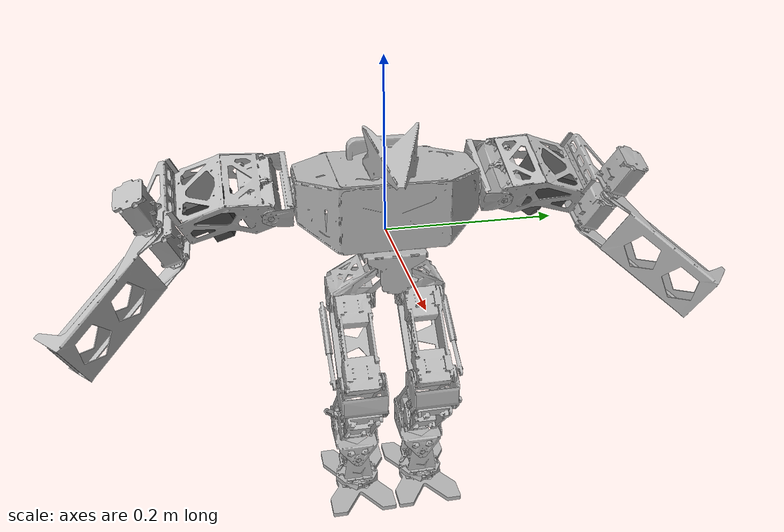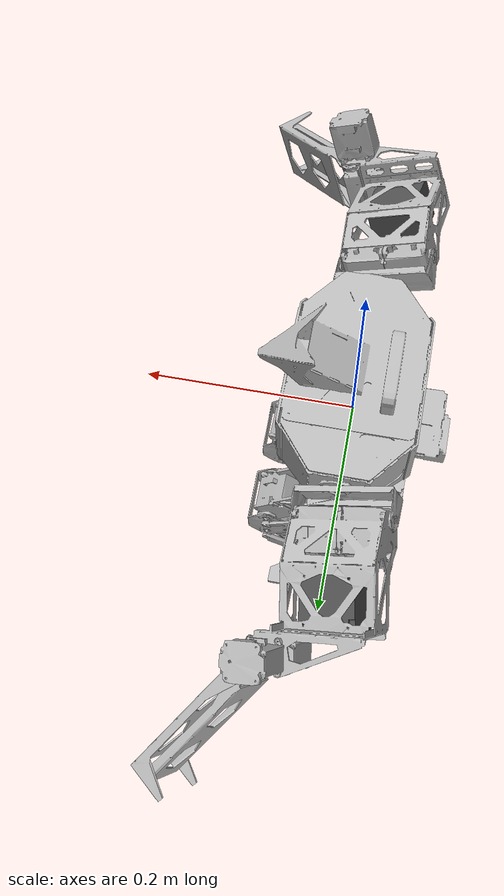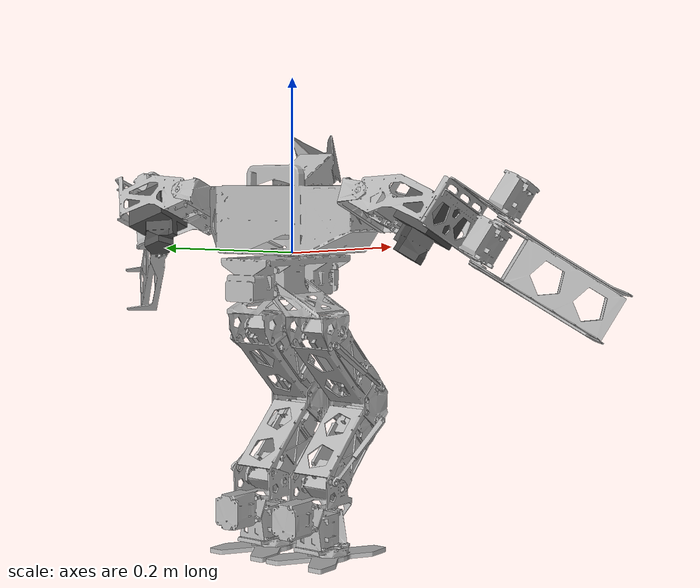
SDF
<sdf version='1.6'>
  <model name='ginko'>
    <link name='body_link0'>
      <pose frame=''>0 0 0 0 -0 0</pose>
      <inertial>
        <pose frame=''>8.3e-05 9e-06 0.038196 0 -0 0</pose>
        <mass>1.41503</mass>
        <inertia>
          <ixx>0.00248548</ixx>
          <ixy>-7.4e-07</ixy>
          <ixz>3.761e-06</ixz>
          <iyy>0.00121388</iyy>
          <iyz>-4.2e-07</iyz>
          <izz>0.00287756</izz>
        </inertia>
      </inertial>
      <collision name='body_link0_collision'>
        <pose frame=''>0 0 0 0 -0 0</pose>
        <geometry>
          <mesh>
            <scale>1 1 1</scale>
            <uri>model://ginko_description/meshes/stl/link00_chest.stl</uri>
          </mesh>
        </geometry>
        <surface>
          <contact>
            <ode>
              <kp>1e+06</kp>
              <kd>100</kd>
              <max_vel>1</max_vel>
              <min_depth>0.0001</min_depth>
            </ode>
          </contact>
          <friction>
            <ode>
              <mu>1</mu>
            </ode>
          </friction>
        </surface>
        <max_contacts>5</max_contacts>
      </collision>
      <visual name='body_link0_visual'>
        <pose frame=''>0 0 0 0 -0 0</pose>
        <geometry>
          <mesh>
            <scale>1 1 1</scale>
            <uri>model://ginko_description/meshes/obj/link00_chest.obj</uri>
          </mesh>
        </geometry>
        <material>
          <script>
            <uri>__default__</uri>
            <name>__default__</name>
          </script>
        </material>
      </visual>
      <gravity>1</gravity>
      <velocity_decay/>
      <self_collide>0</self_collide>
    </link>
    <link name='arm_l_link0'>
      <pose frame=''>0 0.10683 0.05115 0 0.3927 0</pose>
      <inertial>
        <pose frame=''>-0.011258 0.005293 0 0 -0 0</pose>
        <mass>0.0135601</mass>
        <inertia>
          <ixx>2.35e-06</ixx>
          <ixy>4e-08</ixy>
          <ixz>0</ixz>
          <iyy>1.67e-05</iyy>
          <iyz>0</iyz>
          <izz>1.606e-05</izz>
        </inertia>
      </inertial>
      <collision name='arm_l_link0_collision'>
        <pose frame=''>0 0 0 0 -0 0</pose>
        <geometry>
          <mesh>
            <scale>1 1 1</scale>
            <uri>model://ginko_description/meshes/stl/link09_l_arm01.stl</uri>
          </mesh>
        </geometry>
        <surface>
          <contact>
            <ode>
              <kp>1e+06</kp>
              <kd>100</kd>
              <max_vel>1</max_vel>
              <min_depth>0.0001</min_depth>
            </ode>
          </contact>
          <friction>
            <ode>
              <mu>1</mu>
            </ode>
          </friction>
        </surface>
        <max_contacts>5</max_contacts>
      </collision>
      <visual name='arm_l_link0_visual'>
        <pose frame=''>0 0 0 0 -0 0</pose>
        <geometry>
          <mesh>
            <scale>1 1 1</scale>
            <uri>model://ginko_description/meshes/obj/link09_l_arm01.obj</uri>
          </mesh>
        </geometry>
        <material>
          <script>
            <uri>__default__</uri>
            <name>__default__</name>
          </script>
        </material>
      </visual>
      <gravity>1</gravity>
      <velocity_decay/>
      <self_collide>0</self_collide>
    </link>
    <joint name='arm_l_joint0' type='revolute'>
      <child>arm_l_link0</child>
      <parent>body_link0</parent>
      <axis>
        <xyz>0 -1 0</xyz>
        <limit>
          <lower>-2.6</lower>
          <upper>2.6</upper>
          <effort>100</effort>
          <velocity>10</velocity>
        </limit>
        <dynamics>
          <spring_reference>0</spring_reference>
          <spring_stiffness>0</spring_stiffness>
          <damping>0.02</damping>
          <friction>0.0</friction>
        </dynamics>
        <use_parent_model_frame>1</use_parent_model_frame>
      </axis>
    </joint>
    <link name='arm_l_link1'>
      <pose frame=''>0.032336 0.13143 0.037756 1.1781 0.3927 0</pose>
      <inertial>
        <pose frame=''>-0.026128 0.026506 -0.063334 0 -0 0</pose>
        <mass>0.331399</mass>
        <inertia>
          <ixx>0.00115128</ixx>
          <ixy>0.00015366</ixy>
          <ixz>-0.00031848</ixz>
          <iyy>0.00113572</iyy>
          <iyz>-0.00037104</iyz>
          <izz>0.00064743</izz>
        </inertia>
      </inertial>
      <collision name='arm_l_link1_collision'>
        <pose frame=''>0 0 0 0 -0 0</pose>
        <geometry>
          <mesh>
            <scale>1 1 1</scale>
            <uri>model://ginko_description/meshes/stl/link10_l_arm02.stl</uri>
          </mesh>
        </geometry>
        <surface>
          <contact>
            <ode>
              <kp>1e+06</kp>
              <kd>100</kd>
              <max_vel>1</max_vel>
              <min_depth>0.0001</min_depth>
            </ode>
          </contact>
          <friction>
            <ode>
              <mu>1</mu>
            </ode>
          </friction>
        </surface>
        <max_contacts>5</max_contacts>
      </collision>
      <visual name='arm_l_link1_visual'>
        <pose frame=''>0 0 0 0 -0 0</pose>
        <geometry>
          <mesh>
            <scale>1 1 1</scale>
            <uri>model://ginko_description/meshes/obj/link10_l_arm02.obj</uri>
          </mesh>
        </geometry>
        <material>
          <script>
            <uri>__default__</uri>
            <name>__default__</name>
          </script>
        </material>
      </visual>
      <gravity>1</gravity>
      <velocity_decay/>
      <self_collide>0</self_collide>
    </link>
    <joint name='arm_l_joint1' type='revolute'>
      <child>arm_l_link1</child>
      <parent>arm_l_link0</parent>
      <axis>
        <xyz>0.923879 -0 -0.382684</xyz>
        <limit>
          <lower>-0.85</lower>
          <upper>1.18</upper>
          <effort>100</effort>
          <velocity>10</velocity>
        </limit>
        <dynamics>
          <spring_reference>0</spring_reference>
          <spring_stiffness>0</spring_stiffness>
          <damping>0.02</damping>
          <friction>0.0</friction>
        </dynamics>
        <use_parent_model_frame>1</use_parent_model_frame>
      </axis>
    </joint>
    <link name='arm_l_link2'>
      <pose frame=''>0.043634 0.256715 0.040991 1.59493 0.54755 0.871268</pose>
      <inertial>
        <pose frame=''>0.082349 -0.030247 0.005141 0 -0 0</pose>
        <mass>0.0328785</mass>
        <inertia>
          <ixx>2.277e-05</ixx>
          <ixy>-1.4e-07</ixy>
          <ixz>-5.8e-07</ixz>
          <iyy>8.197e-05</iyy>
          <iyz>-1e-08</iyz>
          <izz>0.00010105</izz>
        </inertia>
      </inertial>
      <collision name='arm_l_link2_collision'>
        <pose frame=''>0 0 0 0 -0 0</pose>
        <geometry>
          <mesh>
            <scale>1 1 1</scale>
            <uri>model://ginko_description/meshes/stl/link11_l_scissor01.stl</uri>
          </mesh>
        </geometry>
        <surface>
          <contact>
            <ode>
              <kp>1e+06</kp>
              <kd>100</kd>
              <max_vel>1</max_vel>
              <min_depth>0.0001</min_depth>
            </ode>
          </contact>
          <friction>
            <ode>
              <mu>1</mu>
            </ode>
          </friction>
        </surface>
        <max_contacts>5</max_contacts>
      </collision>
      <visual name='arm_l_link2_visual'>
        <pose frame=''>0 0 0 0 -0 0</pose>
        <geometry>
          <mesh>
            <scale>1 1 1</scale>
            <uri>model://ginko_description/meshes/obj/link11_l_scissor01.obj</uri>
          </mesh>
        </geometry>
        <material>
          <script>
            <uri>__default__</uri>
            <name>__default__</name>
          </script>
        </material>
      </visual>
      <gravity>1</gravity>
      <velocity_decay/>
      <self_collide>0</self_collide>
    </link>
    <joint name='arm_l_joint2' type='revolute'>
      <child>arm_l_link2</child>
      <parent>arm_l_link1</parent>
      <axis>
        <xyz>0.353555 0.382681 0.853554</xyz>
        <limit>
          <lower>-2.36</lower>
          <upper>2.36</upper>
          <effort>100</effort>
          <velocity>10</velocity>
        </limit>
        <dynamics>
          <spring_reference>0</spring_reference>
          <spring_stiffness>0</spring_stiffness>
          <damping>0.02</damping>
          <friction>0.0</friction>
        </dynamics>
        <use_parent_model_frame>1</use_parent_model_frame>
      </axis>
    </joint>
    <link name='arm_l_link3'>
      <pose frame=''>0.023658 0.235093 -0.007235 1.59493 0.54755 0.871268</pose>
      <inertial>
        <pose frame=''>0.07807 0.025152 -0.006654 0 -0 0</pose>
        <mass>0.0293611</mass>
        <inertia>
          <ixx>1.452e-05</ixx>
          <ixy>2.3e-07</ixy>
          <ixz>-2.45e-06</ixz>
          <iyy>6.407e-05</iyy>
          <iyz>-2e-08</iyz>
          <izz>8.024e-05</izz>
        </inertia>
      </inertial>
      <collision name='arm_l_link3_collision'>
        <pose frame=''>0 0 0 0 -0 0</pose>
        <geometry>
          <mesh>
            <scale>1 1 1</scale>
            <uri>model://ginko_description/meshes/stl/link12_l_scissor02.stl</uri>
          </mesh>
        </geometry>
        <surface>
          <contact>
            <ode>
              <kp>1e+06</kp>
              <kd>100</kd>
              <max_vel>1</max_vel>
              <min_depth>0.0001</min_depth>
            </ode>
          </contact>
          <friction>
            <ode>
              <mu>1</mu>
            </ode>
          </friction>
        </surface>
        <max_contacts>5</max_contacts>
      </collision>
      <visual name='arm_l_link3_visual'>
        <pose frame=''>0 0 0 0 -0 0</pose>
        <geometry>
          <mesh>
            <scale>1 1 1</scale>
            <uri>model://ginko_description/meshes/obj/link12_l_scissor02.obj</uri>
          </mesh>
        </geometry>
        <material>
          <script>
            <uri>__default__</uri>
            <name>__default__</name>
          </script>
        </material>
      </visual>
      <gravity>1</gravity>
      <velocity_decay/>
      <self_collide>0</self_collide>
    </link>
    <joint name='arm_l_joint3' type='revolute'>
      <child>arm_l_link3</child>
      <parent>arm_l_link1</parent>
      <axis>
        <xyz>0.353555 0.382681 0.853554</xyz>
        <limit>
          <lower>-2.36</lower>
          <upper>2.36</upper>
          <effort>100</effort>
          <velocity>10</velocity>
        </limit>
        <dynamics>
          <spring_reference>0</spring_reference>
          <spring_stiffness>0</spring_stiffness>
          <damping>0.02</damping>
          <friction>0.0</friction>
        </dynamics>
        <use_parent_model_frame>1</use_parent_model_frame>
      </axis>
    </joint>
    <link name='arm_l_urg_link'>
      <pose frame=''>-0.025808 0.187645 0.016544 -2.72079 0.362091 1.72835</pose>
      <inertial>
        <pose frame=''>-0.000146 8e-06 -0.023605 0 -0 0</pose>
        <mass>0.167055</mass>
        <inertia>
          <ixx>8.801e-05</ixx>
          <ixy>0</ixy>
          <ixz>-4.9e-07</ixz>
          <iyy>8.854e-05</iyy>
          <iyz>-4e-08</iyz>
          <izz>6.019e-05</izz>
        </inertia>
      </inertial>
      <collision name='arm_l_urg_link_collision'>
        <pose frame=''>0 0 0 0 -0 0</pose>
        <geometry>
          <mesh>
            <scale>1 1 1</scale>
            <uri>model://ginko_description/meshes/stl/urg.stl</uri>
          </mesh>
        </geometry>
      </collision>
      <visual name='arm_l_urg_link_visual'>
        <pose frame=''>0 0 0 0 -0 0</pose>
        <geometry>
          <mesh>
            <scale>1 1 1</scale>
            <uri>model://ginko_description/meshes/obj/urg.obj</uri>
          </mesh>
        </geometry>
      </visual>
    </link>
    <joint name='arm_l_urg_joint' type='revolute'>
      <child>arm_l_urg_link</child>
      <parent>arm_l_link1</parent>
      <axis>
        <xyz>-0.352702 -0.383416 -0.853577</xyz>
        <limit>
          <lower>0</lower>
          <upper>0</upper>
          <effort>0</effort>
          <velocity>0</velocity>
        </limit>
        <dynamics>
          <spring_reference>0</spring_reference>
          <spring_stiffness>0</spring_stiffness>
          <damping>0.02</damping>
          <friction>0.0</friction>
        </dynamics>
        <use_parent_model_frame>1</use_parent_model_frame>
      </axis>
    </joint>
    <link name='arm_r_link0'>
      <pose frame=''>0 -0.10683 0.05115 0 0.3927 0</pose>
      <inertial>
        <pose frame=''>-0.011258 -0.005293 0 0 -0 0</pose>
        <mass>0.0135601</mass>
        <inertia>
          <ixx>2.35e-06</ixx>
          <ixy>-4e-08</ixy>
          <ixz>0</ixz>
          <iyy>1.67e-05</iyy>
          <iyz>0</iyz>
          <izz>1.606e-05</izz>
        </inertia>
      </inertial>
      <collision name='arm_r_link0_collision'>
        <pose frame=''>0 0 0 0 -0 0</pose>
        <geometry>
          <mesh>
            <scale>1 1 1</scale>
            <uri>model://ginko_description/meshes/stl/link09_r_arm01.stl</uri>
          </mesh>
        </geometry>
        <surface>
          <contact>
            <ode>
              <kp>1e+06</kp>
              <kd>100</kd>
              <max_vel>1</max_vel>
              <min_depth>0.0001</min_depth>
            </ode>
          </contact>
          <friction>
            <ode>
              <mu>1</mu>
            </ode>
          </friction>
        </surface>
        <max_contacts>5</max_contacts>
      </collision>
      <visual name='arm_r_link0_visual'>
        <pose frame=''>0 0 0 0 -0 0</pose>
        <geometry>
          <mesh>
            <scale>1 1 1</scale>
            <uri>model://ginko_description/meshes/obj/link09_r_arm01.obj</uri>
          </mesh>
        </geometry>
        <material>
          <script>
            <uri>__default__</uri>
            <name>__default__</name>
          </script>
        </material>
      </visual>
      <gravity>1</gravity>
      <velocity_decay/>
      <self_collide>0</self_collide>
    </link>
    <joint name='arm_r_joint0' type='revolute'>
      <child>arm_r_link0</child>
      <parent>body_link0</parent>
      <axis>
        <xyz>0 1 0</xyz>
        <limit>
          <lower>-2.6</lower>
          <upper>2.6</upper>
          <effort>100</effort>
          <velocity>10</velocity>
        </limit>
        <dynamics>
          <spring_reference>0</spring_reference>
          <spring_stiffness>0</spring_stiffness>
          <damping>0.02</damping>
          <friction>0.0</friction>
        </dynamics>
        <use_parent_model_frame>1</use_parent_model_frame>
      </axis>
    </joint>
    <link name='arm_r_link1'>
      <pose frame=''>0.032336 -0.13143 0.037756 -1.1781 0.3927 0</pose>
      <inertial>
        <pose frame=''>-0.026128 -0.026506 -0.063334 0 -0 0</pose>
        <mass>0.331399</mass>
        <inertia>
          <ixx>0.00115128</ixx>
          <ixy>-0.00015366</ixy>
          <ixz>-0.00031848</ixz>
          <iyy>0.00113572</iyy>
          <iyz>0.00037104</iyz>
          <izz>0.00064743</izz>
        </inertia>
      </inertial>
      <collision name='arm_r_link1_collision'>
        <pose frame=''>0 0 0 0 -0 0</pose>
        <geometry>
          <mesh>
            <scale>1 1 1</scale>
            <uri>model://ginko_description/meshes/stl/link10_r_arm02.stl</uri>
          </mesh>
        </geometry>
        <surface>
          <contact>
            <ode>
              <kp>1e+06</kp>
              <kd>100</kd>
              <max_vel>1</max_vel>
              <min_depth>0.0001</min_depth>
            </ode>
          </contact>
          <friction>
            <ode>
              <mu>1</mu>
            </ode>
          </friction>
        </surface>
        <max_contacts>5</max_contacts>
      </collision>
      <visual name='arm_r_link1_visual'>
        <pose frame=''>0 0 0 0 -0 0</pose>
        <geometry>
          <mesh>
            <scale>1 1 1</scale>
            <uri>model://ginko_description/meshes/obj/link10_r_arm02.obj</uri>
          </mesh>
        </geometry>
        <material>
          <script>
            <uri>__default__</uri>
            <name>__default__</name>
          </script>
        </material>
      </visual>
      <gravity>1</gravity>
      <velocity_decay/>
      <self_collide>0</self_collide>
    </link>
    <joint name='arm_r_joint1' type='revolute'>
      <child>arm_r_link1</child>
      <parent>arm_r_link0</parent>
      <axis>
        <xyz>0.923879 0 -0.382684</xyz>
        <limit>
          <lower>-0.85</lower>
          <upper>1.18</upper>
          <effort>100</effort>
          <velocity>10</velocity>
        </limit>
        <dynamics>
          <spring_reference>0</spring_reference>
          <spring_stiffness>0</spring_stiffness>
          <damping>0.02</damping>
          <friction>0.0</friction>
        </dynamics>
        <use_parent_model_frame>1</use_parent_model_frame>
      </axis>
    </joint>
    <link name='arm_r_link2'>
      <pose frame=''>0.043634 -0.256715 0.040991 -1.59493 0.54755 -0.871268</pose>
      <inertial>
        <pose frame=''>0.082349 0.030247 0.005141 0 -0 0</pose>
        <mass>0.0328785</mass>
        <inertia>
          <ixx>2.277e-05</ixx>
          <ixy>1.4e-07</ixy>
          <ixz>-5.8e-07</ixz>
          <iyy>8.197e-05</iyy>
          <iyz>1e-08</iyz>
          <izz>0.00010105</izz>
        </inertia>
      </inertial>
      <collision name='arm_r_link2_collision'>
        <pose frame=''>0 0 0 0 -0 0</pose>
        <geometry>
          <mesh>
            <scale>1 1 1</scale>
            <uri>model://ginko_description/meshes/stl/link11_r_scissor01.stl</uri>
          </mesh>
        </geometry>
        <surface>
          <contact>
            <ode>
              <kp>1e+06</kp>
              <kd>100</kd>
              <max_vel>1</max_vel>
              <min_depth>0.0001</min_depth>
            </ode>
          </contact>
          <friction>
            <ode>
              <mu>1</mu>
            </ode>
          </friction>
        </surface>
        <max_contacts>5</max_contacts>
      </collision>
      <visual name='arm_r_link2_visual'>
        <pose frame=''>0 0 0 0 -0 0</pose>
        <geometry>
          <mesh>
            <scale>1 1 1</scale>
            <uri>model://ginko_description/meshes/obj/link11_r_scissor01.obj</uri>
          </mesh>
        </geometry>
        <material>
          <script>
            <uri>__default__</uri>
            <name>__default__</name>
          </script>
        </material>
      </visual>
      <gravity>1</gravity>
      <velocity_decay/>
      <self_collide>0</self_collide>
    </link>
    <joint name='arm_r_joint2' type='revolute'>
      <child>arm_r_link2</child>
      <parent>arm_r_link1</parent>
      <axis>
        <xyz>0.353555 -0.382681 0.853554</xyz>
        <limit>
          <lower>-2.36</lower>
          <upper>2.36</upper>
          <effort>100</effort>
          <velocity>10</velocity>
        </limit>
        <dynamics>
          <spring_reference>0</spring_reference>
          <spring_stiffness>0</spring_stiffness>
          <damping>0.02</damping>
          <friction>0.0</friction>
        </dynamics>
        <use_parent_model_frame>1</use_parent_model_frame>
      </axis>
    </joint>
    <link name='arm_r_link3'>
      <pose frame=''>0.023658 -0.235093 -0.007235 -1.59493 0.54755 -0.871268</pose>
      <inertial>
        <pose frame=''>0.07807 -0.025152 -0.006654 0 -0 0</pose>
        <mass>0.0293611</mass>
        <inertia>
          <ixx>1.452e-05</ixx>
          <ixy>-2.3e-07</ixy>
          <ixz>-2.45e-06</ixz>
          <iyy>6.407e-05</iyy>
          <iyz>2e-08</iyz>
          <izz>8.024e-05</izz>
        </inertia>
      </inertial>
      <collision name='arm_r_link3_collision'>
        <pose frame=''>0 0 0 0 -0 0</pose>
        <geometry>
          <mesh>
            <scale>1 1 1</scale>
            <uri>model://ginko_description/meshes/stl/link12_r_scissor02.stl</uri>
          </mesh>
        </geometry>
        <surface>
          <contact>
            <ode>
              <kp>1e+06</kp>
              <kd>100</kd>
              <max_vel>1</max_vel>
              <min_depth>0.0001</min_depth>
            </ode>
          </contact>
          <friction>
            <ode>
              <mu>1</mu>
            </ode>
          </friction>
        </surface>
        <max_contacts>5</max_contacts>
      </collision>
      <visual name='arm_r_link3_visual'>
        <pose frame=''>0 0 0 0 -0 0</pose>
        <geometry>
          <mesh>
            <scale>1 1 1</scale>
            <uri>model://ginko_description/meshes/obj/link12_r_scissor02.obj</uri>
          </mesh>
        </geometry>
        <material>
          <script>
            <uri>__default__</uri>
            <name>__default__</name>
          </script>
        </material>
      </visual>
      <gravity>1</gravity>
      <velocity_decay/>
      <self_collide>0</self_collide>
    </link>
    <joint name='arm_r_joint3' type='revolute'>
      <child>arm_r_link3</child>
      <parent>arm_r_link1</parent>
      <axis>
        <xyz>0.353555 -0.382681 0.853554</xyz>
        <limit>
          <lower>-2.36</lower>
          <upper>2.36</upper>
          <effort>100</effort>
          <velocity>10</velocity>
        </limit>
        <dynamics>
          <spring_reference>0</spring_reference>
          <spring_stiffness>0</spring_stiffness>
          <damping>0.02</damping>
          <friction>0.0</friction>
        </dynamics>
        <use_parent_model_frame>1</use_parent_model_frame>
      </axis>
    </joint>
    <link name='arm_r_urg_link'>
      <pose frame=''>-0.025808 -0.187645 0.016544 2.72079 0.362091 -1.72835</pose>
      <inertial>
        <pose frame=''>-0.000146 8e-06 -0.023605 0 -0 0</pose>
        <mass>0.167055</mass>
        <inertia>
          <ixx>8.801e-05</ixx>
          <ixy>0</ixy>
          <ixz>-4.9e-07</ixz>
          <iyy>8.854e-05</iyy>
          <iyz>-4e-08</iyz>
          <izz>6.019e-05</izz>
        </inertia>
      </inertial>
      <collision name='arm_r_urg_link_collision'>
        <pose frame=''>0 0 0 0 -0 0</pose>
        <geometry>
          <mesh>
            <scale>1 1 1</scale>
            <uri>model://ginko_description/meshes/stl/urg.stl</uri>
          </mesh>
        </geometry>
      </collision>
      <visual name='arm_r_urg_link_visual'>
        <pose frame=''>0 0 0 0 -0 0</pose>
        <geometry>
          <mesh>
            <scale>1 1 1</scale>
            <uri>model://ginko_description/meshes/obj/urg.obj</uri>
          </mesh>
        </geometry>
      </visual>
    </link>
    <joint name='arm_r_urg_joint' type='revolute'>
      <child>arm_r_urg_link</child>
      <parent>arm_r_link1</parent>
      <axis>
        <xyz>-0.352702 0.383416 -0.853577</xyz>
        <limit>
          <lower>0</lower>
          <upper>0</upper>
          <effort>0</effort>
          <velocity>0</velocity>
        </limit>
        <dynamics>
          <spring_reference>0</spring_reference>
          <spring_stiffness>0</spring_stiffness>
          <damping>0.02</damping>
          <friction>0.0</friction>
        </dynamics>
        <use_parent_model_frame>1</use_parent_model_frame>
      </axis>
    </joint>
    <link name='body_link1'>
      <pose frame=''>0 0 0 0 -0 0</pose>
      <inertial>
        <pose frame=''>-0.011355 -1e-06 -0.027202 0 -0 0</pose>
        <mass>0.333127</mass>
        <inertia>
          <ixx>0.00015328</ixx>
          <ixy>3e-08</ixy>
          <ixz>1.078e-05</ixz>
          <iyy>0.00073745</iyy>
          <iyz>0</iyz>
          <izz>0.00073107</izz>
        </inertia>
      </inertial>
      <collision name='body_link1_collision'>
        <pose frame=''>0 0 0 0 -0 0</pose>
        <geometry>
          <mesh>
            <scale>1 1 1</scale>
            <uri>model://ginko_description/meshes/stl/link01_waist.stl</uri>
          </mesh>
        </geometry>
        <surface>
          <contact>
            <ode>
              <kp>1e+06</kp>
              <kd>100</kd>
              <max_vel>1</max_vel>
              <min_depth>0.0001</min_depth>
            </ode>
          </contact>
          <friction>
            <ode>
              <mu>1</mu>
            </ode>
          </friction>
        </surface>
        <max_contacts>5</max_contacts>
      </collision>
      <visual name='body_link1_visual'>
        <pose frame=''>0 0 0 0 -0 0</pose>
        <geometry>
          <mesh>
            <scale>1 1 1</scale>
            <uri>model://ginko_description/meshes/obj/link01_waist.obj</uri>
          </mesh>
        </geometry>
        <material>
          <script>
            <uri>__default__</uri>
            <name>__default__</name>
          </script>
        </material>
      </visual>
      <gravity>1</gravity>
      <velocity_decay/>
      <self_collide>0</self_collide>
    </link>
    <joint name='body_joint1' type='revolute'>
      <child>body_link1</child>
      <parent>body_link0</parent>
      <axis>
        <xyz>0 0 1</xyz>
        <limit>
          <lower>-2.6</lower>
          <upper>2.6</upper>
          <effort>100</effort>
          <velocity>10</velocity>
        </limit>
        <dynamics>
          <spring_reference>0</spring_reference>
          <spring_stiffness>0</spring_stiffness>
          <damping>0.1</damping>
          <friction>0.0</friction>
        </dynamics>
        <use_parent_model_frame>1</use_parent_model_frame>
      </axis>
    </joint>
    <link name='leg_l_link0'>
      <pose frame=''>-0.0404 0 -0.0409 0 -0 0</pose>
      <inertial>
        <pose frame=''>0.029308 0.037238 -0.026054 0 -0 0</pose>
        <mass>0.0343335</mass>
        <inertia>
          <ixx>2.443e-05</ixx>
          <ixy>-2.1e-07</ixy>
          <ixz>-2.1e-07</ixz>
          <iyy>2.287e-05</iyy>
          <iyz>-3.91e-06</iyz>
          <izz>2.983e-05</izz>
        </inertia>
      </inertial>
      <collision name='leg_l_link0_collision'>
        <pose frame=''>0 0 0 0 -0 0</pose>
        <geometry>
          <mesh>
            <scale>1 1 1</scale>
            <uri>model://ginko_description/meshes/stl/link02_l_femoral.stl</uri>
          </mesh>
        </geometry>
        <surface>
          <contact>
            <ode>
              <kp>1e+06</kp>
              <kd>100</kd>
              <max_vel>3</max_vel>
              <min_depth>0.0001</min_depth>
            </ode>
          </contact>
          <friction>
            <ode>
              <mu>0</mu>
            </ode>
          </friction>
        </surface>
        <max_contacts>5</max_contacts>
      </collision>
      <visual name='leg_l_link0_visual'>
        <pose frame=''>0 0 0 0 -0 0</pose>
        <geometry>
          <mesh>
            <scale>1 1 1</scale>
            <uri>model://ginko_description/meshes/obj/link02_l_femoral.obj</uri>
          </mesh>
        </geometry>
        <material>
          <script>
            <uri>__default__</uri>
            <name>__default__</name>
          </script>
        </material>
      </visual>
      <gravity>1</gravity>
      <velocity_decay>
        <linear>0.01</linear>
        <angular>0.01</angular>
      </velocity_decay>
      <self_collide>0</self_collide>
    </link>
    <joint name='leg_l_joint0' type='revolute'>
      <child>leg_l_link0</child>
      <parent>body_link1</parent>
      <axis>
        <xyz>-1 0 0</xyz>
        <limit>
          <lower>-0.8</lower>
          <upper>1.1781</upper>
          <effort>100</effort>
          <velocity>10</velocity>
        </limit>
        <dynamics>
          <spring_reference>0</spring_reference>
          <spring_stiffness>0</spring_stiffness>
          <damping>0.02</damping>
          <friction>0.0</friction>
        </dynamics>
        <use_parent_model_frame>1</use_parent_model_frame>
      </axis>
    </joint>
    <link name='leg_l_link1'>
      <pose frame=''>0.0029 0.0175 -0.089 0 0.7854 0</pose>
      <inertial>
        <pose frame=''>0.05 0.032851 0.000681 0 -0 0</pose>
        <mass>0.185257</mass>
        <inertia>
          <ixx>0.00041331</ixx>
          <ixy>-3.605e-05</ixy>
          <ixz>-0</ixz>
          <iyy>0.00027917</iyy>
          <iyz>-1.84e-06</iyz>
          <izz>0.0006651</izz>
        </inertia>
      </inertial>
      <collision name='leg_l_link1_collision'>
        <pose frame=''>0 0 0 0 -0 0</pose>
        <geometry>
          <mesh>
            <scale>1 1 1</scale>
            <uri>model://ginko_description/meshes/stl/link03_l_leg01.stl</uri>
          </mesh>
        </geometry>
        <surface>
          <contact>
            <ode>
              <kp>1e+06</kp>
              <kd>100</kd>
              <max_vel>3</max_vel>
              <min_depth>0.0001</min_depth>
            </ode>
          </contact>
          <friction>
            <ode>
              <mu>0</mu>
            </ode>
          </friction>
        </surface>
        <max_contacts>5</max_contacts>
      </collision>
      <visual name='leg_l_link1_visual'>
        <pose frame=''>0 0 0 0 -0 0</pose>
        <geometry>
          <mesh>
            <scale>1 1 1</scale>
            <uri>model://ginko_description/meshes/obj/link03_l_leg01.obj</uri>
          </mesh>
        </geometry>
        <material>
          <script>
            <uri>__default__</uri>
            <name>__default__</name>
          </script>
        </material>
      </visual>
      <gravity>1</gravity>
      <velocity_decay>
        <linear>0.01</linear>
        <angular>0.01</angular>
      </velocity_decay>
      <self_collide>0</self_collide>
    </link>
    <joint name='leg_l_joint1' type='revolute'>
      <child>leg_l_link1</child>
      <parent>leg_l_link0</parent>
      <axis>
        <xyz>0 -1 0</xyz>
        <limit>
          <lower>-1.3</lower>
          <upper>0.7854</upper>
          <effort>100</effort>
          <velocity>10</velocity>
        </limit>
        <dynamics>
          <spring_reference>0</spring_reference>
          <spring_stiffness>0</spring_stiffness>
          <damping>0.02</damping>
          <friction>0.0</friction>
        </dynamics>
        <use_parent_model_frame>1</use_parent_model_frame>
      </axis>
    </joint>
    <link name='leg_l_link3'>
      <pose frame=''>0.073611 0.0175 -0.159711 0 -0 0</pose>
      <inertial>
        <pose frame=''>0.003934 0.023642 -0.0193 0 -0 0</pose>
        <mass>0.0178118</mass>
        <inertia>
          <ixx>1.301e-05</ixx>
          <ixy>8e-08</ixy>
          <ixz>0</ixz>
          <iyy>7e-06</iyy>
          <iyz>0</iyz>
          <izz>1.388e-05</izz>
        </inertia>
      </inertial>
      <collision name='leg_l_link3_collision'>
        <pose frame=''>0 0 0 0 -0 0</pose>
        <geometry>
          <mesh>
            <scale>1 1 1</scale>
            <uri>model://ginko_description/meshes/stl/link05_l_knee.stl</uri>
          </mesh>
        </geometry>
        <surface>
          <contact>
            <ode>
              <kp>1e+06</kp>
              <kd>100</kd>
              <max_vel>3</max_vel>
              <min_depth>0.0001</min_depth>
            </ode>
          </contact>
          <friction>
            <ode>
              <mu>0.3</mu>
            </ode>
          </friction>
        </surface>
        <max_contacts>5</max_contacts>
      </collision>
      <visual name='leg_l_link3_visual'>
        <pose frame=''>0 0 0 0 -0 0</pose>
        <geometry>
          <mesh>
            <scale>1 1 1</scale>
            <uri>model://ginko_description/meshes/obj/link05_l_knee.obj</uri>
          </mesh>
        </geometry>
        <material>
          <script>
            <uri>__default__</uri>
            <name>__default__</name>
          </script>
        </material>
      </visual>
      <gravity>1</gravity>
      <velocity_decay>
        <linear>0.01</linear>
        <angular>0.01</angular>
      </velocity_decay>
      <self_collide>0</self_collide>
    </link>
    <joint name='leg_l_joint3' type='revolute'>
      <child>leg_l_link3</child>
      <parent>leg_l_link1</parent>
      <axis>
        <xyz>0 1 0</xyz>
        <limit>
          <lower>-1.3</lower>
          <upper>0.7854</upper>
          <effort>100</effort>
          <velocity>10</velocity>
        </limit>
        <dynamics>
          <spring_reference>0</spring_reference>
          <spring_stiffness>0</spring_stiffness>
          <damping>0.02</damping>
          <friction>0.0</friction>
        </dynamics>
        <use_parent_model_frame>1</use_parent_model_frame>
      </axis>
    </joint>

    <joint name='leg_l_joint3_sub' type='revolute'>
      <pose>-0.021 0 -0.012 0 0 0</pose>
      <child>leg_l_link3</child>
      <parent>leg_l_link2</parent>
      <axis>
        <xyz>0 1 0</xyz>
        <limit>
          <lower>-1.3</lower>
          <upper>0.7854</upper>
          <effort>1000</effort>
          <velocity>0.5</velocity>
        </limit>
        <dynamics>
          <spring_reference>0</spring_reference>
          <spring_stiffness>0</spring_stiffness>
        </dynamics>
        <use_parent_model_frame>1</use_parent_model_frame>
      </axis>
    </joint>

    <joint name='leg_l_joint3_spring' type='revolute'>
      <pose>0.0 0.058 0.0 0 0 0</pose>
      <child>leg_l_link3</child>
      <parent>leg_l_spring_link1</parent>
      <axis>
        <xyz>0 1 0</xyz>
        <limit>
          <lower>-3.14159</lower>
          <upper>3.14159</upper>
        </limit>
        <dynamics>
          <spring_reference>0.0</spring_reference>
          <spring_stiffness>0.0</spring_stiffness>
        </dynamics>
        <use_parent_model_frame>1</use_parent_model_frame>
      </axis>
    </joint>

    <link name='leg_l_link4'>
      <pose frame=''>0.073611 0.0175 -0.198311 3.14159 0.785393 3.14159</pose>
      <inertial>
        <pose frame=''>0.05 0.032851 0.000681 0 -0 0</pose>
        <mass>0.185257</mass>
        <inertia>
          <ixx>0.00041331</ixx>
          <ixy>-3.605e-05</ixy>
          <ixz>-0</ixz>
          <iyy>0.00027917</iyy>
          <iyz>-1.84e-06</iyz>
          <izz>0.0006651</izz>
        </inertia>
      </inertial>
      <collision name='leg_l_link4_collision'>
        <pose frame=''>0 0 0 0 -0 0</pose>
        <geometry>
          <mesh>
            <scale>1 1 1</scale>
            <uri>model://ginko_description/meshes/stl/link03_l_leg01.stl</uri>
          </mesh>
        </geometry>
        <surface>
          <contact>
            <ode>
              <kp>1e+06</kp>
              <kd>100</kd>
              <max_vel>3</max_vel>
              <min_depth>0.0001</min_depth>
            </ode>
          </contact>
          <friction>
            <ode>
              <mu>0</mu>
            </ode>
          </friction>
        </surface>
        <max_contacts>5</max_contacts>
      </collision>
      <visual name='leg_l_link4_visual'>
        <pose frame=''>0 0 0 0 -0 0</pose>
        <geometry>
          <mesh>
            <scale>1 1 1</scale>
            <uri>model://ginko_description/meshes/obj/link03_l_leg01.obj</uri>
          </mesh>
        </geometry>
        <material>
          <script>
            <uri>__default__</uri>
            <name>__default__</name>
          </script>
        </material>
      </visual>
      <gravity>1</gravity>
      <velocity_decay>
        <linear>0.01</linear>
        <angular>0.01</angular>
      </velocity_decay>
      <self_collide>0</self_collide>
    </link>
    <joint name='leg_l_joint4' type='revolute'>
      <child>leg_l_link4</child>
      <parent>leg_l_link3</parent>
      <axis>
        <xyz>0 -1 0</xyz>
        <limit>
          <lower>-0.7854</lower>
          <upper>1.3</upper>
          <effort>100</effort>
          <velocity>10</velocity>
        </limit>
        <dynamics>
          <spring_reference>0</spring_reference>
          <spring_stiffness>0</spring_stiffness>
          <damping>0.02</damping>
          <friction>0.0</friction>
        </dynamics>
        <use_parent_model_frame>1</use_parent_model_frame>
      </axis>
    </joint>
    <link name='leg_l_link6'>
      <pose frame=''>0.002899 0.0175 -0.269021 0 -0 0</pose>
      <inertial>
        <pose frame=''>-0.041661 0.024639 -0.025863 0 -0 0</pose>
        <mass>0.087992</mass>
        <inertia>
          <ixx>2.815e-05</ixx>
          <ixy>-4.1e-07</ixy>
          <ixz>9.8e-06</ixz>
          <iyy>6.846e-05</iyy>
          <iyz>-2.6e-07</iyz>
          <izz>6.529e-05</izz>
        </inertia>
      </inertial>
      <collision name='leg_l_link6_collision'>
        <pose frame=''>0 0 0 0 -0 0</pose>
        <geometry>
          <mesh>
            <scale>1 1 1</scale>
            <uri>model://ginko_description/meshes/stl/link06_l_toe01.stl</uri>
          </mesh>
        </geometry>
        <surface>
          <contact>
            <ode>
              <kp>1e+06</kp>
              <kd>100</kd>
              <max_vel>3</max_vel>
              <min_depth>0.0001</min_depth>
            </ode>
          </contact>
          <friction>
            <ode>
              <mu>0</mu>
            </ode>
          </friction>
        </surface>
        <max_contacts>5</max_contacts>
      </collision>
      <visual name='leg_l_link6_visual'>
        <pose frame=''>0 0 0 0 -0 0</pose>
        <geometry>
          <mesh>
            <scale>1 1 1</scale>
            <uri>model://ginko_description/meshes/obj/link06_l_toe01.obj</uri>
          </mesh>
        </geometry>
        <material>
          <script>
            <uri>__default__</uri>
            <name>__default__</name>
          </script>
        </material>
      </visual>
      <gravity>1</gravity>
      <velocity_decay>
        <linear>0.01</linear>
        <angular>0.01</angular>
      </velocity_decay>
      <self_collide>0</self_collide>
    </link>
    <joint name='leg_l_joint6' type='revolute'>
      <child>leg_l_link6</child>
      <parent>leg_l_link4</parent>
      <axis>
        <xyz>0 1 0</xyz>
        <limit>
          <lower>-3.14159</lower>
          <upper>3.14159</upper>
          <effort>100</effort>
          <velocity>10</velocity>
        </limit>
        <dynamics>
          <spring_reference>0</spring_reference>
          <spring_stiffness>0</spring_stiffness>
          <damping>0.02</damping>
          <friction>0.0</friction>
        </dynamics>
        <use_parent_model_frame>1</use_parent_model_frame>
      </axis>
    </joint>

    <joint name='leg_l_joint6_sub' type='revolute'>
      <pose>-0.021 0 0.012 0 0 0</pose>
      <child>leg_l_link6</child>
      <parent>leg_l_link5</parent>
      <pose>-0.1 0 0 0 0 0</pose>
      <axis>
        <xyz>0 1 0</xyz>
        <limit>
          <lower>-3.14159</lower>
          <upper>3.14159</upper>
          <effort>1000</effort>
          <velocity>0.5</velocity>
        </limit>
        <dynamics>
          <spring_reference>0</spring_reference>
          <spring_stiffness>0</spring_stiffness>
        </dynamics>
        <use_parent_model_frame>1</use_parent_model_frame>
      </axis>
    </joint>
    <joint name='leg_l_joint6_spring' type='revolute'>
      <pose>-0.021 0.058 0.012 0 0 0</pose>
      <child>leg_l_link6</child>
      <parent>leg_l_spring_link3</parent>
      <axis>
        <xyz>0 1 0</xyz>
        <limit>
          <lower>-3.14159</lower>
          <upper>3.14159</upper>
        </limit>
        <dynamics>
          <spring_reference>0.0</spring_reference>
          <spring_stiffness>0.0</spring_stiffness>
        </dynamics>
        <use_parent_model_frame>1</use_parent_model_frame>
      </axis>
    </joint>
    <link name='leg_l_link7'>
      <pose frame=''>-0.025101 0.04225 -0.308121 0 -0 0</pose>
      <inertial>
        <pose frame=''>0.026588 1e-06 -0.017825 0 -0 0</pose>
        <mass>0.1092</mass>
        <inertia>
          <ixx>3.853e-05</ixx>
          <ixy>0</ixy>
          <ixz>-4.79e-06</ixz>
          <iyy>5.192e-05</iyy>
          <iyz>0</iyz>
          <izz>3.521e-05</izz>
        </inertia>
      </inertial>
      <collision name='leg_l_link7_collision'>
        <pose frame=''>0 0 0 0 -0 0</pose>
        <geometry>
          <mesh>
            <scale>1 1 1</scale>
            <uri>model://ginko_description/meshes/stl/link07_l_toe02.stl</uri>
          </mesh>
        </geometry>
        <surface>
          <contact>
            <ode>
              <kp>1e+06</kp>
              <kd>100</kd>
              <max_vel>3</max_vel>
              <min_depth>0.0001</min_depth>
            </ode>
          </contact>
          <friction>
            <ode>
              <mu>0</mu>
            </ode>
          </friction>
        </surface>
        <max_contacts>5</max_contacts>
      </collision>
      <visual name='leg_l_link7_visual'>
        <pose frame=''>0 0 0 0 -0 0</pose>
        <geometry>
          <mesh>
            <scale>1 1 1</scale>
            <uri>model://ginko_description/meshes/obj/link07_l_toe02.obj</uri>
          </mesh>
        </geometry>
        <material>
          <script>
            <uri>__default__</uri>
            <name>__default__</name>
          </script>
        </material>
      </visual>
      <gravity>1</gravity>
      <velocity_decay>
        <linear>0.01</linear>
        <angular>0.01</angular>
      </velocity_decay>
      <self_collide>0</self_collide>
    </link>
    <joint name='leg_l_joint7' type='revolute'>
      <child>leg_l_link7</child>
      <parent>leg_l_link6</parent>
      <axis>
        <xyz>-1 0 0</xyz>
        <limit>
          <lower>-1.6</lower>
          <upper>1.6</upper>
          <effort>100</effort>
          <velocity>10</velocity>
        </limit>
        <dynamics>
          <spring_reference>0</spring_reference>
          <spring_stiffness>0</spring_stiffness>
          <damping>0.02</damping>
          <friction>0.0</friction>
        </dynamics>
        <use_parent_model_frame>1</use_parent_model_frame>
      </axis>
    </joint>
    <link name='leg_l_link8'>
      <pose frame=''>0.009099 0.04225 -0.348121 0 -0 0</pose>
      <inertial>
        <pose frame=''>0 0 -0.002693 0 -0 0</pose>
        <mass>0.0536311</mass>
        <inertia>
          <ixx>2.877e-05</ixx>
          <ixy>0</ixy>
          <ixz>0</ixz>
          <iyy>7.083e-05</iyy>
          <iyz>-0</iyz>
          <izz>9.934e-05</izz>
        </inertia>
      </inertial>
      <collision name='leg_l_link8_collision'>
        <pose frame=''>0 0 -0.003 0 0 0</pose>
        <geometry>
          <box>
            <size>0.128 0.08 0.006</size>
          </box>
        </geometry>
        <surface>
          <contact>
            <ode>
              <kp>1e+06</kp>
              <kd>100</kd>
              <max_vel>10</max_vel>
              <min_depth>0.0001</min_depth>
            </ode>
          </contact>
          <friction>
            <ode>
              <mu>1</mu>
            </ode>
          </friction>
        </surface>
        <max_contacts>8</max_contacts>
      </collision>
      <visual name='leg_l_link8_visual'>
        <pose frame=''>0 0 0 0 -0 0</pose>
        <geometry>
          <mesh>
            <scale>1 1 1</scale>
            <uri>model://ginko_description/meshes/obj/link08_l_toe03.obj</uri>
          </mesh>
        </geometry>
        <material>
          <script>
            <uri>__default__</uri>
            <name>__default__</name>
          </script>
        </material>
      </visual>
      <gravity>1</gravity>
      <velocity_decay>
        <linear>0.01</linear>
        <angular>0.01</angular>
      </velocity_decay>
      <self_collide>1</self_collide>
    </link>
    <joint name='leg_l_joint8' type='revolute'>
      <child>leg_l_link8</child>
      <parent>leg_l_link7</parent>
      <axis>
        <xyz>0 0 1</xyz>
        <limit>
          <lower>-2.6</lower>
          <upper>2.6</upper>
          <effort>100</effort>
          <velocity>10</velocity>
        </limit>
        <dynamics>
          <spring_reference>0</spring_reference>
          <spring_stiffness>0</spring_stiffness>
          <damping>0.02</damping>
          <friction>0.0</friction>
        </dynamics>
        <use_parent_model_frame>1</use_parent_model_frame>
      </axis>
    </joint>
    <link name='leg_l_link5'>
      <pose frame=''>0.052311 0.0175 -0.186261 3.14159 0.785393 3.14159</pose>
      <inertial>
        <pose frame=''>0.05 0.024951 -0.004912 0 -0 0</pose>
        <mass>0.0164664</mass>
        <inertia>
          <ixx>6.4e-06</ixx>
          <ixy>0</ixy>
          <ixz>0</ixz>
          <iyy>1.642e-05</iyy>
          <iyz>0</iyz>
          <izz>2.264e-05</izz>
        </inertia>
      </inertial>
      <collision name='leg_l_link5_collision'>
        <pose frame=''>0 0 0 0 -0 0</pose>
        <geometry>
          <mesh>
            <scale>1 1 1</scale>
            <uri>model://ginko_description/meshes/stl/link04_l_leg02.stl</uri>
          </mesh>
        </geometry>
        <surface>
          <contact>
            <ode>
              <kp>1e+06</kp>
              <kd>100</kd>
              <max_vel>3</max_vel>
              <min_depth>0.0001</min_depth>
            </ode>
          </contact>
          <friction>
            <ode>
              <mu>0</mu>
            </ode>
          </friction>
        </surface>
        <max_contacts>5</max_contacts>
      </collision>
      <visual name='leg_l_link5_visual'>
        <pose frame=''>0 0 0 0 -0 0</pose>
        <geometry>
          <mesh>
            <scale>1 1 1</scale>
            <uri>model://ginko_description/meshes/obj/link04_l_leg02.obj</uri>
          </mesh>
        </geometry>
        <material>
          <script>
            <uri>__default__</uri>
            <name>__default__</name>
          </script>
        </material>
      </visual>
      <gravity>1</gravity>
      <velocity_decay>
        <linear>0.01</linear>
        <angular>0.01</angular>
      </velocity_decay>
      <self_collide>0</self_collide>
    </link>
    <joint name='leg_l_joint5' type='revolute'>
      <child>leg_l_link5</child>
      <parent>leg_l_link3</parent>
      <axis>
        <xyz>0 -1 0</xyz>
        <limit>
          <lower>-3.14159</lower>
          <upper>3.14159</upper>
          <effort>100</effort>
          <velocity>10</velocity>
        </limit>
        <dynamics>
          <spring_reference>0</spring_reference>
          <spring_stiffness>0</spring_stiffness>
          <damping>0.02</damping>
          <friction>0.0</friction>
        </dynamics>
        <use_parent_model_frame>1</use_parent_model_frame>
      </axis>
    </joint>
    <link name='leg_l_spring_link2'>
      <pose frame=''>0.073611 0.0755 -0.198311 3.14159 0.567568 3.14159</pose>
      <inertial>
        <pose frame=''>0.030917 0 0 3.14159 1.00323 3.14159</pose>
        <mass>0.00143865</mass>
        <inertia>
          <ixx>1e-08</ixx>
          <ixy>0</ixy>
          <ixz>0</ixz>
          <iyy>6e-07</iyy>
          <iyz>0</iyz>
          <izz>6e-07</izz>
        </inertia>
      </inertial>
      <collision name='leg_l_spring_link2_collision'>
        <pose frame=''>0 0 0 0 -0 0</pose>
        <geometry>
          <mesh>
            <scale>1 1 1</scale>
            <uri>model://ginko_description/meshes/stl/spring1.stl</uri>
          </mesh>
        </geometry>
        <surface>
          <contact>
            <ode>
              <kp>1e+06</kp>
              <kd>100</kd>
              <max_vel>3</max_vel>
              <min_depth>0.0001</min_depth>
            </ode>
          </contact>
          <friction>
            <ode>
              <mu>1</mu>
            </ode>
          </friction>
        </surface>
        <max_contacts>1</max_contacts>
      </collision>
      <visual name='leg_l_spring_link2_visual'>
        <pose frame=''>0 0 0 0 -0 0</pose>
        <geometry>
          <mesh>
            <scale>1 1 1</scale>
            <uri>model://ginko_description/meshes/stl/spring1.stl</uri>
          </mesh>
        </geometry>
        <material>
          <script>
            <uri>__default__</uri>
            <name>__default__</name>
          </script>
        </material>
      </visual>
      <gravity>1</gravity>
      <velocity_decay>
        <linear>0.01</linear>
        <angular>0.01</angular>
      </velocity_decay>
      <self_collide>0</self_collide>
    </link>
    <joint name='leg_l_spring_joint2' type='revolute'>
      <child>leg_l_spring_link2</child>
      <parent>leg_l_link3</parent>
      <axis>
        <xyz>0 -1 0</xyz>
        <limit>
          <lower>-3.14</lower>
          <upper>3.14</upper>
          <effort>0</effort>
          <velocity>10</velocity>
        </limit>
        <dynamics>
          <spring_reference>0</spring_reference>
          <spring_stiffness>0</spring_stiffness>
          <damping>0.02</damping>
          <friction>0.0</friction>
        </dynamics>
        <use_parent_model_frame>1</use_parent_model_frame>
      </axis>
    </joint>
    <link name='leg_l_spring_link3'>
      <pose frame=''>-0.0184 0.0755 -0.256971 0 -0.567567 0</pose>
      <inertial>
        <pose frame=''>0.030917 0 0 0 -0 0</pose>
        <mass>0.00143865</mass>
        <inertia>
          <ixx>1e-08</ixx>
          <ixy>0</ixy>
          <ixz>0</ixz>
          <iyy>6e-07</iyy>
          <iyz>0</iyz>
          <izz>6e-07</izz>
        </inertia>
      </inertial>
      <collision name='leg_l_spring_link3_collision'>
        <pose frame=''>0 0 0 0 -0 0</pose>
        <geometry>
          <mesh>
            <scale>1 1 1</scale>
            <uri>model://ginko_description/meshes/stl/spring2.stl</uri>
          </mesh>
        </geometry>
        <surface>
          <contact>
            <ode>
              <kp>1e+06</kp>
              <kd>100</kd>
              <max_vel>3</max_vel>
              <min_depth>0.0001</min_depth>
            </ode>
          </contact>
          <friction>
            <ode>
              <mu>1</mu>
            </ode>
          </friction>
        </surface>
        <max_contacts>1</max_contacts>
      </collision>
      <visual name='leg_l_spring_link3_visual'>
        <pose frame=''>0 0 0 0 -0 0</pose>
        <geometry>
          <mesh>
            <scale>1 1 1</scale>
            <uri>model://ginko_description/meshes/stl/spring2.stl</uri>
          </mesh>
        </geometry>
        <material>
          <script>
            <uri>__default__</uri>
            <name>__default__</name>
          </script>
        </material>
      </visual>
      <gravity>1</gravity>
      <velocity_decay>
        <linear>0.01</linear>
        <angular>0.01</angular>
      </velocity_decay>
      <self_collide>0</self_collide>
    </link>
    <joint name='leg_l_spring_joint3' type='prismatic'>
      <child>leg_l_spring_link3</child>
      <parent>leg_l_spring_link2</parent>
      <axis>
        <xyz>0.843211 0 0.537582</xyz>
        <limit>
          <lower>-0.038</lower>
          <upper>0.055</upper>
          <effort>0</effort>
          <velocity>10</velocity>
        </limit>
        <dynamics>
          <spring_reference>0.0517</spring_reference>
          <spring_stiffness>457.0</spring_stiffness>
          <damping>0.1</damping>
          <friction>0.0</friction>
        </dynamics>
        <use_parent_model_frame>1</use_parent_model_frame>
      </axis>
    </joint>
    <link name='leg_l_link2'>
      <pose frame=''>-0.0184 0.0175 -0.10105 0 0.7854 0</pose>
      <inertial>
        <pose frame=''>0.05 0.024951 -0.004912 0 -0 0</pose>
        <mass>0.0164664</mass>
        <inertia>
          <ixx>6.4e-06</ixx>
          <ixy>0</ixy>
          <ixz>0</ixz>
          <iyy>1.642e-05</iyy>
          <iyz>0</iyz>
          <izz>2.264e-05</izz>
        </inertia>
      </inertial>
      <collision name='leg_l_link2_collision'>
        <pose frame=''>0 0 0 0 -0 0</pose>
        <geometry>
          <mesh>
            <scale>1 1 1</scale>
            <uri>model://ginko_description/meshes/stl/link04_l_leg02.stl</uri>
          </mesh>
        </geometry>
        <surface>
          <contact>
            <ode>
              <kp>1e+06</kp>
              <kd>100</kd>
              <max_vel>3</max_vel>
              <min_depth>0.0001</min_depth>
            </ode>
          </contact>
          <friction>
            <ode>
              <mu>0</mu>
            </ode>
          </friction>
        </surface>
        <max_contacts>5</max_contacts>
      </collision>
      <visual name='leg_l_link2_visual'>
        <pose frame=''>0 0 0 0 -0 0</pose>
        <geometry>
          <mesh>
            <scale>1 1 1</scale>
            <uri>model://ginko_description/meshes/obj/link04_l_leg02.obj</uri>
          </mesh>
        </geometry>
        <material>
          <script>
            <uri>__default__</uri>
            <name>__default__</name>
          </script>
        </material>
      </visual>
      <gravity>1</gravity>
      <velocity_decay>
        <linear>0.01</linear>
        <angular>0.01</angular>
      </velocity_decay>
      <self_collide>0</self_collide>
    </link>
    <joint name='leg_l_joint2' type='revolute'>
      <child>leg_l_link2</child>
      <parent>leg_l_link0</parent>
      <axis>
        <xyz>0 -1 0</xyz>
        <limit>
          <lower>-1.3</lower>
          <upper>0.7854</upper>
          <effort>100</effort>
          <velocity>10</velocity>
        </limit>
        <dynamics>
          <spring_reference>0</spring_reference>
          <spring_stiffness>0</spring_stiffness>
          <damping>0.02</damping>
          <friction>0.0</friction>
        </dynamics>
        <use_parent_model_frame>1</use_parent_model_frame>
      </axis>
    </joint>
    <link name='leg_l_spring_link0'>
      <pose frame=''>-0.0184 0.0755 -0.10105 0 0.567568 0</pose>
      <inertial>
        <pose frame=''>0.030917 0 0 0 -0 0</pose>
        <mass>0.00143865</mass>
        <inertia>
          <ixx>1e-08</ixx>
          <ixy>0</ixy>
          <ixz>0</ixz>
          <iyy>6e-07</iyy>
          <iyz>0</iyz>
          <izz>6e-07</izz>
        </inertia>
      </inertial>
      <collision name='leg_l_spring_link0_collision'>
        <pose frame=''>0 0 0 0 -0 0</pose>
        <geometry>
          <mesh>
            <scale>1 1 1</scale>
            <uri>model://ginko_description/meshes/stl/spring1.stl</uri>
          </mesh>
        </geometry>
        <surface>
          <contact>
            <ode>
              <kp>1e+06</kp>
              <kd>100</kd>
              <max_vel>3</max_vel>
              <min_depth>0.0001</min_depth>
            </ode>
          </contact>
          <friction>
            <ode>
              <mu>1</mu>
            </ode>
          </friction>
        </surface>
        <max_contacts>1</max_contacts>
      </collision>
      <visual name='leg_l_spring_link0_visual'>
        <pose frame=''>0 0 0 0 -0 0</pose>
        <geometry>
          <mesh>
            <scale>1 1 1</scale>
            <uri>model://ginko_description/meshes/stl/spring1.stl</uri>
          </mesh>
        </geometry>
        <material>
          <script>
            <uri>__default__</uri>
            <name>__default__</name>
          </script>
        </material>
      </visual>
      <gravity>1</gravity>
      <velocity_decay>
        <linear>0.01</linear>
        <angular>0.01</angular>
      </velocity_decay>
      <self_collide>0</self_collide>
    </link>
    <joint name='leg_l_spring_joint0' type='revolute'>
      <child>leg_l_spring_link0</child>
      <parent>leg_l_link0</parent>
      <axis>
        <xyz>0 -1 0</xyz>
        <limit>
          <lower>-3.14159</lower>
          <upper>3.14159</upper>
          <effort>0</effort>
          <velocity>10</velocity>
        </limit>
        <dynamics>
          <spring_reference>0</spring_reference>
          <spring_stiffness>0</spring_stiffness>
          <damping>0.02</damping>
          <friction>0.0</friction>
        </dynamics>
        <use_parent_model_frame>1</use_parent_model_frame>
      </axis>
    </joint>
    <link name='leg_l_spring_link1'>
      <pose frame=''>0.073611 0.0755 -0.159711 3.14159 -0.567568 -3.14159</pose>
      <inertial>
        <pose frame=''>0.030917 0 0 0 -0 0</pose>
        <mass>0.00143865</mass>
        <inertia>
          <ixx>1e-08</ixx>
          <ixy>0</ixy>
          <ixz>0</ixz>
          <iyy>6e-07</iyy>
          <iyz>0</iyz>
          <izz>6e-07</izz>
        </inertia>
      </inertial>
      <collision name='leg_l_spring_link1_collision'>
        <pose frame=''>0 0 0 0 -0 0</pose>
        <geometry>
          <mesh>
            <scale>1 1 1</scale>
            <uri>model://ginko_description/meshes/stl/spring2.stl</uri>
          </mesh>
        </geometry>
        <surface>
          <contact>
            <ode>
              <kp>1e+06</kp>
              <kd>100</kd>
              <max_vel>3</max_vel>
              <min_depth>0.0001</min_depth>
            </ode>
          </contact>
          <friction>
            <ode>
              <mu>1</mu>
            </ode>
          </friction>
        </surface>
        <max_contacts>1</max_contacts>
      </collision>
      <visual name='leg_l_spring_link1_visual'>
        <pose frame=''>0 0 0 0 -0 0</pose>
        <geometry>
          <mesh>
            <scale>1 1 1</scale>
            <uri>model://ginko_description/meshes/stl/spring2.stl</uri>
          </mesh>
        </geometry>
        <material>
          <script>
            <uri>__default__</uri>
            <name>__default__</name>
          </script>
        </material>
      </visual>
      <gravity>1</gravity>
      <velocity_decay>
        <linear>0.01</linear>
        <angular>0.01</angular>
      </velocity_decay>
      <self_collide>0</self_collide>
    </link>
    <joint name='leg_l_spring_joint1' type='prismatic'>
      <child>leg_l_spring_link1</child>
      <parent>leg_l_spring_link0</parent>
      <axis>
        <xyz>-0.843211 0 0.537583</xyz>
        <limit>
          <lower>-0.038</lower>
          <upper>0.055</upper>
          <effort>0</effort>
          <velocity>10</velocity>
        </limit>
        <dynamics>
          <spring_reference>0.0517</spring_reference>
          <spring_stiffness>457.0</spring_stiffness>
          <damping>0.1</damping>
          <friction>0.0</friction>
        </dynamics>
        <use_parent_model_frame>1</use_parent_model_frame>
      </axis>
    </joint>
    <link name='leg_r_link0'>
      <pose frame=''>0.0205 0 -0.0409 0 -0 0</pose>
      <inertial>
        <pose frame=''>-0.029058 -0.037235 -0.02605 0 -0 0</pose>
        <mass>0.0343146</mass>
        <inertia>
          <ixx>2.441e-05</ixx>
          <ixy>1e-08</ixy>
          <ixz>2.1e-07</ixz>
          <iyy>2.285e-05</iyy>
          <iyz>3.91e-06</iyz>
          <izz>2.98e-05</izz>
        </inertia>
      </inertial>
      <collision name='leg_r_link0_collision'>
        <pose frame=''>0 0 0 0 -0 0</pose>
        <geometry>
          <mesh>
            <scale>1 1 1</scale>
            <uri>model://ginko_description/meshes/stl/link02_r_femoral.stl</uri>
          </mesh>
        </geometry>
        <surface>
          <contact>
            <ode>
              <kp>1e+06</kp>
              <kd>100</kd>
              <max_vel>3</max_vel>
              <min_depth>0.0001</min_depth>
            </ode>
          </contact>
          <friction>
            <ode>
              <mu>0</mu>
            </ode>
          </friction>
        </surface>
        <max_contacts>5</max_contacts>
      </collision>
      <visual name='leg_r_link0_visual'>
        <pose frame=''>0 0 0 0 -0 0</pose>
        <geometry>
          <mesh>
            <scale>1 1 1</scale>
            <uri>model://ginko_description/meshes/obj/link02_r_femoral.obj</uri>
          </mesh>
        </geometry>
        <material>
          <script>
            <uri>__default__</uri>
            <name>__default__</name>
          </script>
        </material>
      </visual>
      <gravity>1</gravity>
      <velocity_decay>
        <linear>0.01</linear>
        <angular>0.01</angular>
      </velocity_decay>
      <self_collide>0</self_collide>
    </link>
    <joint name='leg_r_joint0' type='revolute'>
      <child>leg_r_link0</child>
      <parent>body_link1</parent>
      <axis>
        <xyz>1 0 0</xyz>
        <limit>
          <lower>-1.1781</lower>
          <upper>0.8</upper>
          <effort>100</effort>
          <velocity>10</velocity>
        </limit>
        <dynamics>
          <spring_reference>0</spring_reference>
          <spring_stiffness>0</spring_stiffness>
          <damping>0.02</damping>
          <friction>0.0</friction>
        </dynamics>
        <use_parent_model_frame>1</use_parent_model_frame>
      </axis>
    </joint>
    <link name='leg_r_link1'>
      <pose frame=''>0.0029 -0.0175 -0.089 0 0.7854 0</pose>
      <inertial>
        <pose frame=''>0.05 -0.017191 0.000681 0 -0 0</pose>
        <mass>0.185257</mass>
        <inertia>
          <ixx>0.00055489</ixx>
          <ixy>-4.242e-05</ixy>
          <ixz>0</ixz>
          <iyy>0.00027917</iyy>
          <iyz>-1.75e-06</iyz>
          <izz>0.00081028</izz>
        </inertia>
      </inertial>
      <collision name='leg_r_link1_collision'>
        <pose frame=''>0 0 0 0 -0 0</pose>
        <geometry>
          <mesh>
            <scale>1 1 1</scale>
            <uri>model://ginko_description/meshes/stl/link03_r_leg01.stl</uri>
          </mesh>
        </geometry>
        <surface>
          <contact>
            <ode>
              <kp>1e+06</kp>
              <kd>100</kd>
              <max_vel>3</max_vel>
              <min_depth>0.0001</min_depth>
            </ode>
          </contact>
          <friction>
            <ode>
              <mu>0</mu>
            </ode>
          </friction>
        </surface>
        <max_contacts>5</max_contacts>
      </collision>
      <visual name='leg_r_link1_visual'>
        <pose frame=''>0 0 0 0 -0 0</pose>
        <geometry>
          <mesh>
            <scale>1 1 1</scale>
            <uri>model://ginko_description/meshes/obj/link03_r_leg01.obj</uri>
          </mesh>
        </geometry>
        <material>
          <script>
            <uri>__default__</uri>
            <name>__default__</name>
          </script>
        </material>
      </visual>
      <gravity>1</gravity>
      <velocity_decay>
        <linear>0.01</linear>
        <angular>0.01</angular>
      </velocity_decay>
      <self_collide>0</self_collide>
    </link>
    <joint name='leg_r_joint1' type='revolute'>
      <child>leg_r_link1</child>
      <parent>leg_r_link0</parent>
      <axis>
        <xyz>0 1 0</xyz>
        <limit>
          <lower>-0.7854</lower>
          <upper>1.3</upper>
          <effort>100</effort>
          <velocity>10</velocity>
        </limit>
        <dynamics>
          <spring_reference>0</spring_reference>
          <spring_stiffness>0</spring_stiffness>
          <damping>0.02</damping>
          <friction>0.0</friction>
        </dynamics>
        <use_parent_model_frame>1</use_parent_model_frame>
      </axis>
    </joint>
    <link name='leg_r_link3'>
      <pose frame=''>0.073611 -0.0175 -0.159711 0 -0 0</pose>
      <inertial>
        <pose frame=''>0.003934 -0.023642 -0.0193 0 -0 0</pose>
        <mass>0.0178118</mass>
        <inertia>
          <ixx>1.301e-05</ixx>
          <ixy>-8e-08</ixy>
          <ixz>0</ixz>
          <iyy>7e-06</iyy>
          <iyz>0</iyz>
          <izz>1.388e-05</izz>
        </inertia>
      </inertial>
      <collision name='leg_r_link3_collision'>
        <pose frame=''>0 0 0 0 -0 0</pose>
        <geometry>
          <mesh>
            <scale>1 1 1</scale>
            <uri>model://ginko_description/meshes/stl/link05_r_knee.stl</uri>
          </mesh>
        </geometry>
        <surface>
          <contact>
            <ode>
              <kp>1e+06</kp>
              <kd>100</kd>
              <max_vel>3</max_vel>
              <min_depth>0.0001</min_depth>
            </ode>
          </contact>
          <friction>
            <ode>
              <mu>0.3</mu>
            </ode>
          </friction>
        </surface>
        <max_contacts>5</max_contacts>
      </collision>
      <visual name='leg_r_link3_visual'>
        <pose frame=''>0 0 0 0 -0 0</pose>
        <geometry>
          <mesh>
            <scale>1 1 1</scale>
            <uri>model://ginko_description/meshes/obj/link05_r_knee.obj</uri>
          </mesh>
        </geometry>
        <material>
          <script>
            <uri>__default__</uri>
            <name>__default__</name>
          </script>
        </material>
      </visual>
      <gravity>1</gravity>
      <velocity_decay>
        <linear>0.01</linear>
        <angular>0.01</angular>
      </velocity_decay>
      <self_collide>0</self_collide>
    </link>
    <joint name='leg_r_joint3' type='revolute'>
      <child>leg_r_link3</child>
      <parent>leg_r_link1</parent>
      <axis>
        <xyz>0 -1 0</xyz>
        <limit>
          <lower>-0.7854</lower>
          <upper>1.3</upper>
          <effort>100</effort>
          <velocity>10</velocity>
        </limit>
        <dynamics>
          <spring_reference>0</spring_reference>
          <spring_stiffness>0</spring_stiffness>
          <damping>0.02</damping>
          <friction>0.0</friction>
        </dynamics>
        <use_parent_model_frame>1</use_parent_model_frame>
      </axis>
    </joint>

    <joint name='leg_r_joint3_sub' type='revolute'>
      <pose>-0.021 0 -0.012 0 0 0</pose>
      <child>leg_r_link3</child>
      <parent>leg_r_link2</parent>
      <axis>
        <xyz>0 -1 0</xyz>
        <limit>
          <lower>-0.7854</lower>
          <upper>1.3</upper>
          <effort>100</effort>
          <velocity>10</velocity>
        </limit>
        <dynamics>
          <spring_reference>0</spring_reference>
          <spring_stiffness>0</spring_stiffness>
        </dynamics>
        <use_parent_model_frame>1</use_parent_model_frame>
      </axis>
    </joint>

    <joint name='leg_r_joint3_spring' type='revolute'>
      <pose>0.0 -0.058 0.0 0 0 0</pose>
      <child>leg_r_link3</child>
      <parent>leg_r_spring_link1</parent>
      <axis>
        <xyz>0 1 0</xyz>
        <limit>
          <lower>-3.14159</lower>
          <upper>3.14159</upper>
        </limit>
        <dynamics>
          <spring_reference>0.0</spring_reference>
          <spring_stiffness>0.0</spring_stiffness>
        </dynamics>
        <use_parent_model_frame>1</use_parent_model_frame>
      </axis>
    </joint>

    <link name='leg_r_link4'>
      <pose frame=''>0.073611 -0.0175 -0.198311 3.14159 0.785393 3.14159</pose>
      <inertial>
        <pose frame=''>0.05 -0.017191 0.000681 0 -0 0</pose>
        <mass>0.185257</mass>
        <inertia>
          <ixx>0.00055489</ixx>
          <ixy>-4.242e-05</ixy>
          <ixz>0</ixz>
          <iyy>0.00027917</iyy>
          <iyz>-1.75e-06</iyz>
          <izz>0.00081028</izz>
        </inertia>
      </inertial>
      <collision name='leg_r_link4_collision'>
        <pose frame=''>0 0 0 0 -0 0</pose>
        <geometry>
          <mesh>
            <scale>1 1 1</scale>
            <uri>model://ginko_description/meshes/stl/link03_r_leg01.stl</uri>
          </mesh>
        </geometry>
        <surface>
          <contact>
            <ode>
              <kp>1e+06</kp>
              <kd>100</kd>
              <max_vel>3</max_vel>
              <min_depth>0.0001</min_depth>
            </ode>
          </contact>
          <friction>
            <ode>
              <mu>0</mu>
            </ode>
          </friction>
        </surface>
        <max_contacts>5</max_contacts>
      </collision>
      <visual name='leg_r_link4_visual'>
        <pose frame=''>0 0 0 0 -0 0</pose>
        <geometry>
          <mesh>
            <scale>1 1 1</scale>
            <uri>model://ginko_description/meshes/obj/link03_r_leg01.obj</uri>
          </mesh>
        </geometry>
        <material>
          <script>
            <uri>__default__</uri>
            <name>__default__</name>
          </script>
        </material>
      </visual>
      <gravity>1</gravity>
      <velocity_decay>
        <linear>0.01</linear>
        <angular>0.01</angular>
      </velocity_decay>
      <self_collide>0</self_collide>
    </link>
    <joint name='leg_r_joint4' type='revolute'>
      <child>leg_r_link4</child>
      <parent>leg_r_link3</parent>
      <axis>
        <xyz>0 1 0</xyz>
        <limit>
          <lower>-1.3</lower>
          <upper>0.7854</upper>
          <effort>100</effort>
          <velocity>10</velocity>
        </limit>
        <dynamics>
          <spring_reference>0</spring_reference>
          <spring_stiffness>0</spring_stiffness>
          <damping>0.02</damping>
          <friction>0.0</friction>
        </dynamics>
        <use_parent_model_frame>1</use_parent_model_frame>
      </axis>
    </joint>
    <link name='leg_r_link6'>
      <pose frame=''>0.002899 -0.0175 -0.269021 0 -0 0</pose>
      <inertial>
        <pose frame=''>-0.041661 -0.024639 -0.025863 0 -0 0</pose>
        <mass>0.087992</mass>
        <inertia>
          <ixx>2.815e-05</ixx>
          <ixy>4.1e-07</ixy>
          <ixz>9.8e-06</ixz>
          <iyy>6.846e-05</iyy>
          <iyz>2.6e-07</iyz>
          <izz>6.529e-05</izz>
        </inertia>
      </inertial>
      <collision name='leg_r_link6_collision'>
        <pose frame=''>0 0 0 0 -0 0</pose>
        <geometry>
          <mesh>
            <scale>1 1 1</scale>
            <uri>model://ginko_description/meshes/stl/link06_r_toe01.stl</uri>
          </mesh>
        </geometry>
        <surface>
          <contact>
            <ode>
              <kp>1e+06</kp>
              <kd>100</kd>
              <max_vel>3</max_vel>
              <min_depth>0.0001</min_depth>
            </ode>
          </contact>
          <friction>
            <ode>
              <mu>0</mu>
            </ode>
          </friction>
        </surface>
        <max_contacts>5</max_contacts>
      </collision>
      <visual name='leg_r_link6_visual'>
        <pose frame=''>0 0 0 0 -0 0</pose>
        <geometry>
          <mesh>
            <scale>1 1 1</scale>
            <uri>model://ginko_description/meshes/obj/link06_r_toe01.obj</uri>
          </mesh>
        </geometry>
        <material>
          <script>
            <uri>__default__</uri>
            <name>__default__</name>
          </script>
        </material>
      </visual>
      <gravity>1</gravity>
      <velocity_decay>
        <linear>0.01</linear>
        <angular>0.01</angular>
      </velocity_decay>
      <self_collide>0</self_collide>
    </link>
    <joint name='leg_r_joint6' type='revolute'>
      <child>leg_r_link6</child>
      <parent>leg_r_link4</parent>
      <axis>
        <xyz>0 -1 0</xyz>
        <limit>
          <lower>-0.7854</lower>
          <upper>1.3</upper>
          <effort>100</effort>
          <velocity>10</velocity>
        </limit>
        <dynamics>
          <spring_reference>0</spring_reference>
          <spring_stiffness>0</spring_stiffness>
          <damping>0.02</damping>
          <friction>0.0</friction>
        </dynamics>
        <use_parent_model_frame>1</use_parent_model_frame>
      </axis>
    </joint>

    <joint name='leg_r_joint6_sub' type='revolute'>
      <pose>-0.021 0 0.012 0 0 0</pose>
      <child>leg_r_link6</child>
      <parent>leg_r_link5</parent>
      <axis>
        <xyz>0 -1 0</xyz>
        <limit>
          <lower>-0.7854</lower>
          <upper>1.3</upper>
          <effort>100</effort>
          <velocity>10</velocity>
        </limit>
        <dynamics>
          <spring_reference>0</spring_reference>
          <spring_stiffness>0</spring_stiffness>
        </dynamics>
        <use_parent_model_frame>1</use_parent_model_frame>
      </axis>
    </joint>
    <joint name='leg_r_joint6_spring' type='revolute'>
      <pose>-0.021 -0.058 0.012 0 0 0</pose>
      <child>leg_r_link6</child>
      <parent>leg_r_spring_link3</parent>
      <axis>
        <xyz>0 1 0</xyz>
        <limit>
          <lower>-3.14159</lower>
          <upper>3.14159</upper>
        </limit>
        <dynamics>
          <spring_reference>0.0</spring_reference>
          <spring_stiffness>0.0</spring_stiffness>
        </dynamics>
        <use_parent_model_frame>1</use_parent_model_frame>
      </axis>
    </joint>
    <link name='leg_r_link7'>
      <pose frame=''>-0.025101 -0.04225 -0.308121 0 -0 0</pose>
      <inertial>
        <pose frame=''>0.026588 -1e-06 -0.017825 0 -0 0</pose>
        <mass>0.1092</mass>
        <inertia>
          <ixx>3.853e-05</ixx>
          <ixy>0</ixy>
          <ixz>-4.79e-06</ixz>
          <iyy>5.192e-05</iyy>
          <iyz>0</iyz>
          <izz>3.521e-05</izz>
        </inertia>
      </inertial>
      <collision name='leg_r_link7_collision'>
        <pose frame=''>0 0 0 0 -0 0</pose>
        <geometry>
          <mesh>
            <scale>1 1 1</scale>
            <uri>model://ginko_description/meshes/stl/link07_r_toe02.stl</uri>
          </mesh>
        </geometry>
        <surface>
          <contact>
            <ode>
              <kp>1e+06</kp>
              <kd>100</kd>
              <max_vel>3</max_vel>
              <min_depth>0.0001</min_depth>
            </ode>
          </contact>
          <friction>
            <ode>
              <mu>0</mu>
            </ode>
          </friction>
        </surface>
        <max_contacts>5</max_contacts>
      </collision>
      <visual name='leg_r_link7_visual'>
        <pose frame=''>0 0 0 0 -0 0</pose>
        <geometry>
          <mesh>
            <scale>1 1 1</scale>
            <uri>model://ginko_description/meshes/obj/link07_r_toe02.obj</uri>
          </mesh>
        </geometry>
        <material>
          <script>
            <uri>__default__</uri>
            <name>__default__</name>
          </script>
        </material>
      </visual>
      <gravity>1</gravity>
      <velocity_decay>
        <linear>0.01</linear>
        <angular>0.01</angular>
      </velocity_decay>
      <self_collide>0</self_collide>
    </link>
    <joint name='leg_r_joint7' type='revolute'>
      <child>leg_r_link7</child>
      <parent>leg_r_link6</parent>
      <axis>
        <xyz>-1 0 0</xyz>
        <limit>
          <lower>-1.6</lower>
          <upper>1.6</upper>
          <effort>100</effort>
          <velocity>10</velocity>
        </limit>
        <dynamics>
          <spring_reference>0</spring_reference>
          <spring_stiffness>0</spring_stiffness>
          <damping>0.02</damping>
          <friction>0.0</friction>
        </dynamics>
        <use_parent_model_frame>1</use_parent_model_frame>
      </axis>
    </joint>
    <link name='leg_r_link8'>
      <pose frame=''>0.009099 -0.04225 -0.348121 0 -0 0</pose>
      <inertial>
        <pose frame=''>0 0 -0.002693 0 -0 0</pose>
        <mass>0.0536311</mass>
        <inertia>
          <ixx>2.877e-05</ixx>
          <ixy>0</ixy>
          <ixz>0</ixz>
          <iyy>7.083e-05</iyy>
          <iyz>-0</iyz>
          <izz>9.934e-05</izz>
        </inertia>
      </inertial>
      <collision name='leg_r_link8_collision'>
        <pose frame=''>0 0 -0.003 0 0 0</pose>
        <geometry>
          <box>
            <size>0.128 0.08 0.006</size>
          </box>
        </geometry>
        <surface>
          <contact>
            <ode>
              <kp>1e+06</kp>
              <kd>100</kd>
              <max_vel>10</max_vel>
              <min_depth>0.0001</min_depth>
            </ode>
          </contact>
          <friction>
            <ode>
              <mu>1</mu>
            </ode>
          </friction>
        </surface>
        <max_contacts>8</max_contacts>
      </collision>
      <visual name='leg_r_link8_visual'>
        <pose frame=''>0 0 0 0 -0 0</pose>
        <geometry>
          <mesh>
            <scale>1 1 1</scale>
            <uri>model://ginko_description/meshes/obj/link08_r_toe03.obj</uri>
          </mesh>
        </geometry>
        <material>
          <script>
            <uri>__default__</uri>
            <name>__default__</name>
          </script>
        </material>
      </visual>
      <gravity>1</gravity>
      <velocity_decay>
        <linear>0.01</linear>
        <angular>0.01</angular>
      </velocity_decay>
      <self_collide>1</self_collide>
    </link>
    <joint name='leg_r_joint8' type='revolute'>
      <child>leg_r_link8</child>
      <parent>leg_r_link7</parent>
      <axis>
        <xyz>0 0 1</xyz>
        <limit>
          <lower>-2.6</lower>
          <upper>2.6</upper>
          <effort>100</effort>
          <velocity>10</velocity>
        </limit>
        <dynamics>
          <spring_reference>0</spring_reference>
          <spring_stiffness>0</spring_stiffness>
          <damping>0.02</damping>
          <friction>0.0</friction>
        </dynamics>
        <use_parent_model_frame>1</use_parent_model_frame>
      </axis>
    </joint>
    <link name='leg_r_link5'>
      <pose frame=''>0.052311 -0.0175 -0.186261 3.14159 0.785393 3.14159</pose>
      <inertial>
        <pose frame=''>0.05 -0.024951 -0.004912 0 -0 0</pose>
        <mass>0.0164664</mass>
        <inertia>
          <ixx>6.4e-06</ixx>
          <ixy>0</ixy>
          <ixz>0</ixz>
          <iyy>1.642e-05</iyy>
          <iyz>0</iyz>
          <izz>2.264e-05</izz>
        </inertia>
      </inertial>
      <collision name='leg_r_link5_collision'>
        <pose frame=''>0 0 0 0 -0 0</pose>
        <geometry>
          <mesh>
            <scale>1 1 1</scale>
            <uri>model://ginko_description/meshes/stl/link04_r_leg02.stl</uri>
          </mesh>
        </geometry>
        <surface>
          <contact>
            <ode>
              <kp>1e+06</kp>
              <kd>100</kd>
              <max_vel>3</max_vel>
              <min_depth>0.0001</min_depth>
            </ode>
          </contact>
          <friction>
            <ode>
              <mu>0</mu>
            </ode>
          </friction>
        </surface>
        <max_contacts>5</max_contacts>
      </collision>
      <visual name='leg_r_link5_visual'>
        <pose frame=''>0 0 0 0 -0 0</pose>
        <geometry>
          <mesh>
            <scale>1 1 1</scale>
            <uri>model://ginko_description/meshes/obj/link04_r_leg02.obj</uri>
          </mesh>
        </geometry>
        <material>
          <script>
            <uri>__default__</uri>
            <name>__default__</name>
          </script>
        </material>
      </visual>
      <gravity>1</gravity>
      <velocity_decay>
        <linear>0.01</linear>
        <angular>0.01</angular>
      </velocity_decay>
      <self_collide>0</self_collide>
    </link>
    <joint name='leg_r_joint5' type='revolute'>
      <child>leg_r_link5</child>
      <parent>leg_r_link3</parent>
      <axis>
        <xyz>0 1 0</xyz>
        <limit>
          <lower>-3.14159</lower>
          <upper>3.14159</upper>
          <effort>100</effort>
          <velocity>10</velocity>
        </limit>
        <dynamics>
          <spring_reference>0</spring_reference>
          <spring_stiffness>0</spring_stiffness>
          <damping>0.02</damping>
          <friction>0.0</friction>
        </dynamics>
        <use_parent_model_frame>1</use_parent_model_frame>
      </axis>
    </joint>
    <link name='leg_r_spring_link2'>
      <pose frame=''>0.073611 -0.0755 -0.198311 3.14159 0.567568 3.14159</pose>
      <inertial>
        <pose frame=''>0.030917 0 0 3.14159 1.00323 3.14159</pose>
        <mass>0.00143865</mass>
        <inertia>
          <ixx>1e-08</ixx>
          <ixy>0</ixy>
          <ixz>0</ixz>
          <iyy>6e-07</iyy>
          <iyz>0</iyz>
          <izz>6e-07</izz>
        </inertia>
      </inertial>
      <collision name='leg_r_spring_link2_collision'>
        <pose frame=''>0 0 0 0 -0 0</pose>
        <geometry>
          <mesh>
            <scale>1 1 1</scale>
            <uri>model://ginko_description/meshes/stl/spring1.stl</uri>
          </mesh>
        </geometry>
        <surface>
          <contact>
            <ode>
              <kp>1e+06</kp>
              <kd>100</kd>
              <max_vel>3</max_vel>
              <min_depth>0.0001</min_depth>
            </ode>
          </contact>
          <friction>
            <ode>
              <mu>1</mu>
            </ode>
          </friction>
        </surface>
        <max_contacts>1</max_contacts>
      </collision>
      <visual name='leg_r_spring_link2_visual'>
        <pose frame=''>0 0 0 0 -0 0</pose>
        <geometry>
          <mesh>
            <scale>1 1 1</scale>
            <uri>model://ginko_description/meshes/stl/spring1.stl</uri>
          </mesh>
        </geometry>
        <material>
          <script>
            <uri>__default__</uri>
            <name>__default__</name>
          </script>
        </material>
      </visual>
      <gravity>1</gravity>
      <velocity_decay>
        <linear>0.01</linear>
        <angular>0.01</angular>
      </velocity_decay>
      <self_collide>0</self_collide>
    </link>
    <joint name='leg_r_spring_joint2' type='revolute'>
      <child>leg_r_spring_link2</child>
      <parent>leg_r_link3</parent>
      <axis>
        <xyz>0 -1 0</xyz>
        <limit>
          <lower>-3.14159</lower>
          <upper>3.14159</upper>
          <effort>0</effort>
          <velocity>10</velocity>
        </limit>
        <dynamics>
          <spring_reference>0</spring_reference>
          <spring_stiffness>0</spring_stiffness>
          <damping>0.02</damping>
          <friction>0.0</friction>
        </dynamics>
        <use_parent_model_frame>1</use_parent_model_frame>
      </axis>
    </joint>
    <link name='leg_r_spring_link3'>
      <pose frame=''>-0.0184 -0.0755 -0.256971 0 -0.567567 0</pose>
      <inertial>
        <pose frame=''>0.030917 0 0 0 -0 0</pose>
        <mass>0.00143865</mass>
        <inertia>
          <ixx>1e-08</ixx>
          <ixy>0</ixy>
          <ixz>0</ixz>
          <iyy>6e-07</iyy>
          <iyz>0</iyz>
          <izz>6e-07</izz>
        </inertia>
      </inertial>
      <collision name='leg_r_spring_link3_collision'>
        <pose frame=''>0 0 0 0 -0 0</pose>
        <geometry>
          <mesh>
            <scale>1 1 1</scale>
            <uri>model://ginko_description/meshes/stl/spring2.stl</uri>
          </mesh>
        </geometry>
        <surface>
          <contact>
            <ode>
              <kp>1e+06</kp>
              <kd>100</kd>
              <max_vel>3</max_vel>
              <min_depth>0.0001</min_depth>
            </ode>
          </contact>
          <friction>
            <ode>
              <mu>1</mu>
            </ode>
          </friction>
        </surface>
        <max_contacts>1</max_contacts>
      </collision>
      <visual name='leg_r_spring_link3_visual'>
        <pose frame=''>0 0 0 0 -0 0</pose>
        <geometry>
          <mesh>
            <scale>1 1 1</scale>
            <uri>model://ginko_description/meshes/stl/spring2.stl</uri>
          </mesh>
        </geometry>
        <material>
          <script>
            <uri>__default__</uri>
            <name>__default__</name>
          </script>
        </material>
      </visual>
      <gravity>1</gravity>
      <velocity_decay>
        <linear>0.01</linear>
        <angular>0.01</angular>
      </velocity_decay>
      <self_collide>0</self_collide>
    </link>
    <joint name='leg_r_spring_joint3' type='prismatic'>
      <child>leg_r_spring_link3</child>
      <parent>leg_r_spring_link2</parent>
      <axis>
        <xyz>0.843211 0 0.537582</xyz>
        <limit>
          <lower>-0.038</lower>
          <upper>0.055</upper>
          <effort>0</effort>
          <velocity>10</velocity>
        </limit>
        <dynamics>
          <spring_reference>0.0517</spring_reference>
          <spring_stiffness>457.0</spring_stiffness>
          <damping>0.1</damping>
          <friction>0.0</friction>
        </dynamics>
        <use_parent_model_frame>1</use_parent_model_frame>
      </axis>
    </joint>
    <link name='leg_r_link2'>
      <pose frame=''>-0.0184 -0.0175 -0.10105 0 0.7854 0</pose>
      <inertial>
        <pose frame=''>0.05 -0.024951 -0.004912 0 -0 0</pose>
        <mass>0.0164664</mass>
        <inertia>
          <ixx>6.4e-06</ixx>
          <ixy>0</ixy>
          <ixz>0</ixz>
          <iyy>1.642e-05</iyy>
          <iyz>0</iyz>
          <izz>2.264e-05</izz>
        </inertia>
      </inertial>
      <collision name='leg_r_link2_collision'>
        <pose frame=''>0 0 0 0 -0 0</pose>
        <geometry>
          <mesh>
            <scale>1 1 1</scale>
            <uri>model://ginko_description/meshes/stl/link04_r_leg02.stl</uri>
          </mesh>
        </geometry>
        <surface>
          <contact>
            <ode>
              <kp>1e+06</kp>
              <kd>100</kd>
              <max_vel>3</max_vel>
              <min_depth>0.0001</min_depth>
            </ode>
          </contact>
          <friction>
            <ode>
              <mu>0</mu>
            </ode>
          </friction>
        </surface>
        <max_contacts>5</max_contacts>
      </collision>
      <visual name='leg_r_link2_visual'>
        <pose frame=''>0 0 0 0 -0 0</pose>
        <geometry>
          <mesh>
            <scale>1 1 1</scale>
            <uri>model://ginko_description/meshes/obj/link04_r_leg02.obj</uri>
          </mesh>
        </geometry>
        <material>
          <script>
            <uri>__default__</uri>
            <name>__default__</name>
          </script>
        </material>
      </visual>
      <gravity>1</gravity>
      <velocity_decay>
        <linear>0.01</linear>
        <angular>0.01</angular>
      </velocity_decay>
      <self_collide>0</self_collide>
    </link>
    <joint name='leg_r_joint2' type='revolute'>
      <child>leg_r_link2</child>
      <parent>leg_r_link0</parent>
      <axis>
        <xyz>0 1 0</xyz>
        <limit>
          <lower>-0.7854</lower>
          <upper>1.3</upper>
          <effort>100</effort>
          <velocity>10</velocity>
        </limit>
        <dynamics>
          <spring_reference>0</spring_reference>
          <spring_stiffness>0</spring_stiffness>
          <damping>0.02</damping>
          <friction>0.0</friction>
        </dynamics>
        <use_parent_model_frame>1</use_parent_model_frame>
      </axis>
    </joint>
    <link name='leg_r_spring_link0'>
      <pose frame=''>-0.0184 -0.0755 -0.10105 0 0.567568 0</pose>
      <inertial>
        <pose frame=''>0.030917 0 0 0 -0 0</pose>
        <mass>0.00143865</mass>
        <inertia>
          <ixx>1e-08</ixx>
          <ixy>0</ixy>
          <ixz>0</ixz>
          <iyy>6e-07</iyy>
          <iyz>0</iyz>
          <izz>6e-07</izz>
        </inertia>
      </inertial>
      <collision name='leg_r_spring_link0_collision'>
        <pose frame=''>0 0 0 0 -0 0</pose>
        <geometry>
          <mesh>
            <scale>1 1 1</scale>
            <uri>model://ginko_description/meshes/stl/spring1.stl</uri>
          </mesh>
        </geometry>
        <surface>
          <contact>
            <ode>
              <kp>1e+06</kp>
              <kd>100</kd>
              <max_vel>3</max_vel>
              <min_depth>0.0001</min_depth>
            </ode>
          </contact>
          <friction>
            <ode>
              <mu>1</mu>
            </ode>
          </friction>
        </surface>
        <max_contacts>1</max_contacts>
      </collision>
      <visual name='leg_r_spring_link0_visual'>
        <pose frame=''>0 0 0 0 -0 0</pose>
        <geometry>
          <mesh>
            <scale>1 1 1</scale>
            <uri>model://ginko_description/meshes/stl/spring1.stl</uri>
          </mesh>
        </geometry>
        <material>
          <script>
            <uri>__default__</uri>
            <name>__default__</name>
          </script>
        </material>
      </visual>
      <gravity>1</gravity>
      <velocity_decay>
        <linear>0.01</linear>
        <angular>0.01</angular>
      </velocity_decay>
      <self_collide>0</self_collide>
    </link>
    <joint name='leg_r_spring_joint0' type='revolute'>
      <child>leg_r_spring_link0</child>
      <parent>leg_r_link0</parent>
      <axis>
        <xyz>0 -1 0</xyz>
        <limit>
          <lower>-3.14159</lower>
          <upper>3.14159</upper>
          <effort>0</effort>
          <velocity>10</velocity>
        </limit>
        <dynamics>
          <spring_reference>0</spring_reference>
          <spring_stiffness>0</spring_stiffness>
          <damping>0.02</damping>
          <friction>0.0</friction>
        </dynamics>
        <use_parent_model_frame>1</use_parent_model_frame>
      </axis>
    </joint>
    <link name='leg_r_spring_link1'>
      <pose frame=''>0.073611 -0.0755 -0.159711 3.14159 -0.567568 -3.14159</pose>
      <inertial>
        <pose frame=''>0.030917 0 0 0 -0 0</pose>
        <mass>0.00143865</mass>
        <inertia>
          <ixx>1e-08</ixx>
          <ixy>0</ixy>
          <ixz>0</ixz>
          <iyy>6e-07</iyy>
          <iyz>0</iyz>
          <izz>6e-07</izz>
        </inertia>
      </inertial>
      <collision name='leg_r_spring_link1_collision'>
        <pose frame=''>0 0 0 0 -0 0</pose>
        <geometry>
          <mesh>
            <scale>1 1 1</scale>
            <uri>model://ginko_description/meshes/stl/spring2.stl</uri>
          </mesh>
        </geometry>
        <surface>
          <contact>
            <ode>
              <kp>1e+06</kp>
              <kd>100</kd>
              <max_vel>3</max_vel>
              <min_depth>0.0001</min_depth>
            </ode>
          </contact>
          <friction>
            <ode>
              <mu>1</mu>
            </ode>
          </friction>
        </surface>
        <max_contacts>1</max_contacts>
      </collision>
      <visual name='leg_r_spring_link1_visual'>
        <pose frame=''>0 0 0 0 -0 0</pose>
        <geometry>
          <mesh>
            <scale>1 1 1</scale>
            <uri>model://ginko_description/meshes/stl/spring2.stl</uri>
          </mesh>
        </geometry>
        <material>
          <script>
            <uri>__default__</uri>
            <name>__default__</name>
          </script>
        </material>
      </visual>
      <gravity>1</gravity>
      <velocity_decay>
        <linear>0.01</linear>
        <angular>0.01</angular>
      </velocity_decay>
      <self_collide>0</self_collide>
    </link>
    <joint name='leg_r_spring_joint1' type='prismatic'>
      <child>leg_r_spring_link1</child>
      <parent>leg_r_spring_link0</parent>
      <axis>
        <xyz>-0.843211 0 0.537583</xyz>
        <limit>
          <lower>-0.038</lower>
          <upper>0.055</upper>
          <effort>0</effort>
          <velocity>10</velocity>
        </limit>
        <dynamics>
          <spring_reference>0.0517</spring_reference>
          <spring_stiffness>457.0</spring_stiffness>
          <damping>0.1</damping>
          <friction>0.0</friction>
        </dynamics>
        <use_parent_model_frame>1</use_parent_model_frame>
      </axis>
    </joint>
    <static>0</static>
    <plugin name='gazebo_ros_control' filename='libgazebo_ros_control.so'>
      <robotNamespace>/ginko</robotNamespace>
       <legacyModeNS>true</legacyModeNS>
      <robotSimType>gazebo_ros_control/GinkoRobotHWSim</robotSimType>
    </plugin>
  </model>
</sdf>
